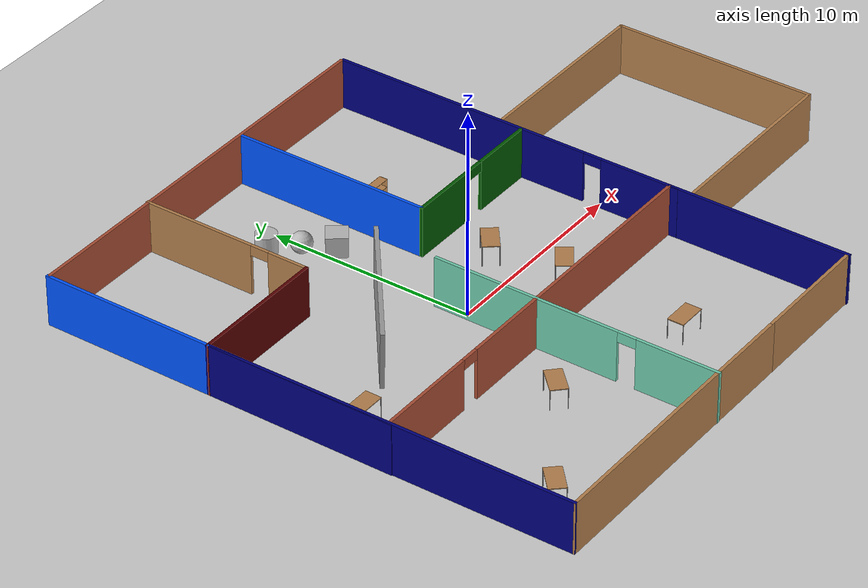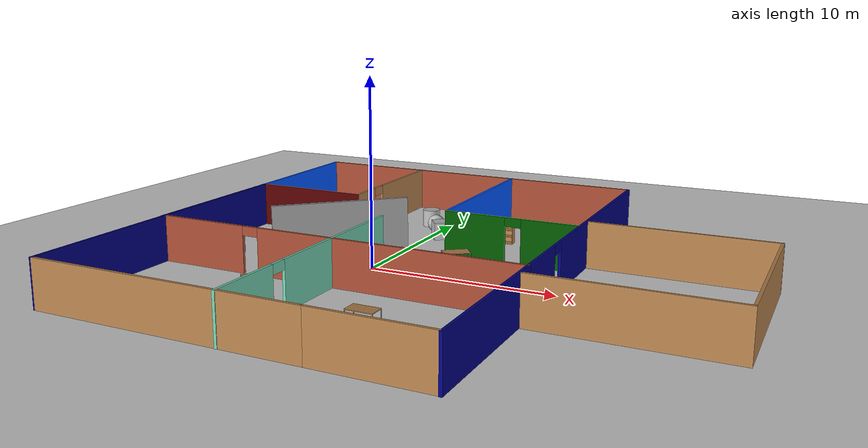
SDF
<sdf version="1.6">
 <world name="default">
  <model name="ground_plane">
   <static>1</static>
   <link name="link">
    <collision name="collision">
     <geometry><plane><normal>0 0 1</normal><size>100 100</size></plane></geometry>
     <surface><friction><ode><mu>100</mu><mu2>50</mu2></ode></friction></surface>
    </collision>
    <visual name="visual">
     <cast_shadows>0</cast_shadows>
     <geometry><plane><normal>0 0 1</normal><size>100 100</size></plane></geometry>
     <material>
      <script><uri>file://media/materials/scripts/gazebo.material</uri><name>Gazebo/Grey</name></script>
     </material>
    </visual>
   </link>
  </model>
  <gravity>0 0 -9.8</gravity>
  <magnetic_field>6e-06 2.3e-05 -4.2e-05</magnetic_field>
  <atmosphere type="adiabatic"/>
  <physics name="default_physics" default="0" type="ode">
   <max_step_size>0.001</max_step_size>
   <real_time_factor>1</real_time_factor>
   <real_time_update_rate>1000</real_time_update_rate>
  </physics>
  <scene><ambient>0.4 0.4 0.4 1</ambient><background>0.7 0.7 0.7 1</background><shadows>1</shadows></scene>
  <spherical_coordinates>
   <surface_model>EARTH_WGS84</surface_model>
   <latitude_deg>0</latitude_deg>
   <longitude_deg>0</longitude_deg>
   <elevation>0</elevation>
   <heading_deg>0</heading_deg>
  </spherical_coordinates>
  <model name="bookshelf">
   <static>1</static>
   <link name="link">
    <inertial><mass>1</mass></inertial>
    <collision name="back">
     <pose>0 0.005 0.6 0 -0 0</pose>
     <geometry><box><size>0.9 0.01 1.2</size></box></geometry>
    </collision>
    <visual name="visual1">
     <pose>0 0.005 0.6 0 -0 0</pose>
     <geometry><box><size>0.9 0.01 1.2</size></box></geometry>
     <material>
      <script><uri>file://media/materials/scripts/gazebo.material</uri><name>Gazebo/Wood</name></script>
     </material>
    </visual>
    <collision name="left_side">
     <pose>0.45 -0.195 0.6 0 -0 0</pose>
     <geometry><box><size>0.02 0.4 1.2</size></box></geometry>
    </collision>
    <visual name="visual2">
     <pose>0.45 -0.195 0.6 0 -0 0</pose>
     <geometry><box><size>0.02 0.4 1.2</size></box></geometry>
     <material>
      <script><uri>file://media/materials/scripts/gazebo.material</uri><name>Gazebo/Wood</name></script>
     </material>
    </visual>
    <collision name="right_side">
     <pose>-0.45 -0.195 0.6 0 -0 0</pose>
     <geometry><box><size>0.02 0.4 1.2</size></box></geometry>
    </collision>
    <visual name="visual3">
     <pose>-0.45 -0.195 0.6 0 -0 0</pose>
     <geometry><box><size>0.02 0.4 1.2</size></box></geometry>
     <material>
      <script><uri>file://media/materials/scripts/gazebo.material</uri><name>Gazebo/Wood</name></script>
     </material>
    </visual>
    <collision name="bottom">
     <pose>0 -0.195 0.03 0 -0 0</pose>
     <geometry><box><size>0.88 0.4 0.06</size></box></geometry>
    </collision>
    <visual name="visual4">
     <pose>0 -0.195 0.03 0 -0 0</pose>
     <geometry><box><size>0.88 0.4 0.06</size></box></geometry>
     <material>
      <script><uri>file://media/materials/scripts/gazebo.material</uri><name>Gazebo/Wood</name></script>
     </material>
    </visual>
    <collision name="top">
     <pose>0 -0.195 1.19 0 -0 0</pose>
     <geometry><box><size>0.88 0.4 0.02</size></box></geometry>
    </collision>
    <visual name="visual5">
     <pose>0 -0.195 1.19 0 -0 0</pose>
     <geometry><box><size>0.88 0.4 0.02</size></box></geometry>
     <material>
      <script><uri>file://media/materials/scripts/gazebo.material</uri><name>Gazebo/Wood</name></script>
     </material>
    </visual>
    <collision name="low_shelf">
     <pose>0 -0.195 0.43 0 -0 0</pose>
     <geometry><box><size>0.88 0.4 0.02</size></box></geometry>
    </collision>
    <visual name="visual6">
     <pose>0 -0.195 0.43 0 -0 0</pose>
     <geometry><box><size>0.88 0.4 0.02</size></box></geometry>
     <material>
      <script><uri>file://media/materials/scripts/gazebo.material</uri><name>Gazebo/Wood</name></script>
     </material>
    </visual>
    <collision name="high_shelf">
     <pose>0 -0.195 0.8 0 -0 0</pose>
     <geometry><box><size>0.88 0.4 0.02</size></box></geometry>
    </collision>
    <visual name="visual7">
     <pose>0 -0.195 0.8 0 -0 0</pose>
     <geometry><box><size>0.88 0.4 0.02</size></box></geometry>
     <material>
      <script><uri>file://media/materials/scripts/gazebo.material</uri><name>Gazebo/Wood</name></script>
     </material>
    </visual>
   </link>
   <pose>4.37362 8.00409 0 0 -0 0</pose>
  </model>
  <model name="table">
   <static>0</static>
   <link name="link">
    <collision name="surface">
     <pose>0 0 1 0 -0 0</pose>
     <geometry><box><size>1.5 0.8 0.03</size></box></geometry>
     <surface><friction><ode><mu>0.6</mu><mu2>0.6</mu2></ode></friction></surface>
    </collision>
    <visual name="visual1">
     <pose>0 0 1 0 -0 0</pose>
     <geometry><box><size>1.4 0.8 0.04</size></box></geometry>
     <material>
      <script><uri>file://media/materials/scripts/gazebo.material</uri><name>Gazebo/Wood</name></script>
     </material>
    </visual>
    <collision name="front_left_leg">
     <pose>0.68 0.38 0.5 0 -0 0</pose>
     <geometry><cylinder><radius>0.02</radius><length>1</length></cylinder></geometry>
    </collision>
    <visual name="front_left_leg">
     <pose>0.68 0.38 0.5 0 -0 0</pose>
     <geometry><cylinder><radius>0.02</radius><length>1</length></cylinder></geometry>
     <material>
      <script><uri>file://media/materials/scripts/gazebo.material</uri><name>Gazebo/Grey</name></script>
     </material>
    </visual>
    <collision name="front_right_leg">
     <pose>0.68 -0.38 0.5 0 -0 0</pose>
     <geometry><cylinder><radius>0.02</radius><length>1</length></cylinder></geometry>
    </collision>
    <visual name="front_right_leg">
     <pose>0.68 -0.38 0.5 0 -0 0</pose>
     <geometry><cylinder><radius>0.02</radius><length>1</length></cylinder></geometry>
     <material>
      <script><uri>file://media/materials/scripts/gazebo.material</uri><name>Gazebo/Grey</name></script>
     </material>
    </visual>
    <collision name="back_right_leg">
     <pose>-0.68 -0.38 0.5 0 -0 0</pose>
     <geometry><cylinder><radius>0.02</radius><length>1</length></cylinder></geometry>
    </collision>
    <visual name="back_right_leg">
     <pose>-0.68 -0.38 0.5 0 -0 0</pose>
     <geometry><cylinder><radius>0.02</radius><length>1</length></cylinder></geometry>
     <material>
      <script><uri>file://media/materials/scripts/gazebo.material</uri><name>Gazebo/Grey</name></script>
     </material>
    </visual>
    <collision name="back_left_leg">
     <pose>-0.68 0.38 0.5 0 -0 0</pose>
     <geometry><cylinder><radius>0.02</radius><length>1</length></cylinder></geometry>
    </collision>
    <visual name="back_left_leg">
     <pose>-0.68 0.38 0.5 0 -0 0</pose>
     <geometry><cylinder><radius>0.02</radius><length>1</length></cylinder></geometry>
     <material>
      <script><uri>file://media/materials/scripts/gazebo.material</uri><name>Gazebo/Grey</name></script>
     </material>
    </visual>
    <inertial>
     <inertia><ixx>1</ixx><ixy>0</ixy><ixz>0</ixz><iyy>1</iyy><iyz>0</iyz><izz>1</izz></inertia>
     <mass>1</mass>
    </inertial>
   </link>
   <pose>-8.45641 -0.835319 -9e-06 0 -0 0</pose>
  </model>
  <model name="textured_shapes">
   <pose>-0.307519 8.3938 0.5 0 -0 0.64384</pose>
   <link name="box">
    <pose>0 -1.5 0 0 -0 0</pose>
    <collision name="collision"><geometry><box><size>1 1 1</size></box></geometry></collision>
    <visual name="visual">
     <geometry><box><size>1 1 1</size></box></geometry>
     <material>
      <script>
       <uri>model://textured_shapes/materials/scripts</uri>
       <uri>model://textured_shapes/materials/textures</uri>
       <name>TexturedShape/Squares</name>
      </script>
     </material>
    </visual>
    <inertial>
     <inertia><ixx>1</ixx><ixy>0</ixy><ixz>0</ixz><iyy>1</iyy><iyz>0</iyz><izz>1</izz></inertia>
     <mass>1</mass>
    </inertial>
   </link>
   <link name="sphere">
    <collision name="collision"><geometry><sphere><radius>0.5</radius></sphere></geometry></collision>
    <visual name="visual">
     <geometry><sphere><radius>0.5</radius></sphere></geometry>
     <material>
      <script>
       <uri>model://textured_shapes/materials/scripts</uri>
       <uri>model://textured_shapes/materials/textures</uri>
       <name>TexturedShape/Squares</name>
      </script>
     </material>
    </visual>
    <inertial>
     <inertia><ixx>1</ixx><ixy>0</ixy><ixz>0</ixz><iyy>1</iyy><iyz>0</iyz><izz>1</izz></inertia>
     <mass>1</mass>
    </inertial>
   </link>
   <link name="cylinder">
    <pose>0 1.5 0 0 -0 0</pose>
    <collision name="collision">
     <geometry><cylinder><radius>0.5</radius><length>1</length></cylinder></geometry>
    </collision>
    <visual name="visual">
     <geometry><cylinder><radius>0.5</radius><length>1</length></cylinder></geometry>
     <material>
      <script>
       <uri>model://textured_shapes/materials/scripts</uri>
       <uri>model://textured_shapes/materials/textures</uri>
       <name>TexturedShape/Squares</name>
      </script>
     </material>
    </visual>
    <inertial>
     <inertia><ixx>1</ixx><ixy>0</ixy><ixz>0</ixz><iyy>1</iyy><iyz>0</iyz><izz>1</izz></inertia>
     <mass>1</mass>
    </inertial>
   </link>
  </model>
  <model name="table_0">
   <static>0</static>
   <link name="link">
    <collision name="surface">
     <pose>0 0 1 0 -0 0</pose>
     <geometry><box><size>1.5 0.8 0.03</size></box></geometry>
     <surface><friction><ode><mu>0.6</mu><mu2>0.6</mu2></ode></friction></surface>
    </collision>
    <visual name="visual1">
     <pose>0 0 1 0 -0 0</pose>
     <geometry><box><size>1.4 0.8 0.04</size></box></geometry>
     <material>
      <script><uri>file://media/materials/scripts/gazebo.material</uri><name>Gazebo/Wood</name></script>
     </material>
    </visual>
    <collision name="front_left_leg">
     <pose>0.68 0.38 0.5 0 -0 0</pose>
     <geometry><cylinder><radius>0.02</radius><length>1</length></cylinder></geometry>
    </collision>
    <visual name="front_left_leg">
     <pose>0.68 0.38 0.5 0 -0 0</pose>
     <geometry><cylinder><radius>0.02</radius><length>1</length></cylinder></geometry>
     <material>
      <script><uri>file://media/materials/scripts/gazebo.material</uri><name>Gazebo/Grey</name></script>
     </material>
    </visual>
    <collision name="front_right_leg">
     <pose>0.68 -0.38 0.5 0 -0 0</pose>
     <geometry><cylinder><radius>0.02</radius><length>1</length></cylinder></geometry>
    </collision>
    <visual name="front_right_leg">
     <pose>0.68 -0.38 0.5 0 -0 0</pose>
     <geometry><cylinder><radius>0.02</radius><length>1</length></cylinder></geometry>
     <material>
      <script><uri>file://media/materials/scripts/gazebo.material</uri><name>Gazebo/Grey</name></script>
     </material>
    </visual>
    <collision name="back_right_leg">
     <pose>-0.68 -0.38 0.5 0 -0 0</pose>
     <geometry><cylinder><radius>0.02</radius><length>1</length></cylinder></geometry>
    </collision>
    <visual name="back_right_leg">
     <pose>-0.68 -0.38 0.5 0 -0 0</pose>
     <geometry><cylinder><radius>0.02</radius><length>1</length></cylinder></geometry>
     <material>
      <script><uri>file://media/materials/scripts/gazebo.material</uri><name>Gazebo/Grey</name></script>
     </material>
    </visual>
    <collision name="back_left_leg">
     <pose>-0.68 0.38 0.5 0 -0 0</pose>
     <geometry><cylinder><radius>0.02</radius><length>1</length></cylinder></geometry>
    </collision>
    <visual name="back_left_leg">
     <pose>-0.68 0.38 0.5 0 -0 0</pose>
     <geometry><cylinder><radius>0.02</radius><length>1</length></cylinder></geometry>
     <material>
      <script><uri>file://media/materials/scripts/gazebo.material</uri><name>Gazebo/Grey</name></script>
     </material>
    </visual>
    <inertial>
     <inertia><ixx>1</ixx><ixy>0</ixy><ixz>0</ixz><iyy>1</iyy><iyz>0</iyz><izz>1</izz></inertia>
     <mass>1</mass>
    </inertial>
   </link>
   <pose>4.11112 -8.08132 -9e-06 0 -0 0</pose>
  </model>
  <model name="grey_wall">
   <static>1</static>
   <link name="link">
    <pose>0 0 1.4 0 -0 0</pose>
    <collision name="collision"><geometry><box><size>7.5 0.2 2.8</size></box></geometry></collision>
    <visual name="visual">
     <cast_shadows>0</cast_shadows>
     <geometry><box><size>7.5 0.2 2.8</size></box></geometry>
     <material>
      <script>
       <uri>model://grey_wall/materials/scripts</uri>
       <uri>model://grey_wall/materials/textures</uri>
       <name>vrc/grey_wall</name>
      </script>
     </material>
    </visual>
   </link>
   <pose>-3.18514 2.23987 4e-06 0.01417 -0.022146 0.663578</pose>
  </model>
  <model name="table_1">
   <static>0</static>
   <link name="link">
    <collision name="surface">
     <pose>0 0 1 0 -0 0</pose>
     <geometry><box><size>1.5 0.8 0.03</size></box></geometry>
     <surface><friction><ode><mu>0.6</mu><mu2>0.6</mu2></ode></friction></surface>
    </collision>
    <visual name="visual1">
     <pose>0 0 1 0 -0 0</pose>
     <geometry><box><size>1.4 0.8 0.04</size></box></geometry>
     <material>
      <script><uri>file://media/materials/scripts/gazebo.material</uri><name>Gazebo/Wood</name></script>
     </material>
    </visual>
    <collision name="front_left_leg">
     <pose>0.68 0.38 0.5 0 -0 0</pose>
     <geometry><cylinder><radius>0.02</radius><length>1</length></cylinder></geometry>
    </collision>
    <visual name="front_left_leg">
     <pose>0.68 0.38 0.5 0 -0 0</pose>
     <geometry><cylinder><radius>0.02</radius><length>1</length></cylinder></geometry>
     <material>
      <script><uri>file://media/materials/scripts/gazebo.material</uri><name>Gazebo/Grey</name></script>
     </material>
    </visual>
    <collision name="front_right_leg">
     <pose>0.68 -0.38 0.5 0 -0 0</pose>
     <geometry><cylinder><radius>0.02</radius><length>1</length></cylinder></geometry>
    </collision>
    <visual name="front_right_leg">
     <pose>0.68 -0.38 0.5 0 -0 0</pose>
     <geometry><cylinder><radius>0.02</radius><length>1</length></cylinder></geometry>
     <material>
      <script><uri>file://media/materials/scripts/gazebo.material</uri><name>Gazebo/Grey</name></script>
     </material>
    </visual>
    <collision name="back_right_leg">
     <pose>-0.68 -0.38 0.5 0 -0 0</pose>
     <geometry><cylinder><radius>0.02</radius><length>1</length></cylinder></geometry>
    </collision>
    <visual name="back_right_leg">
     <pose>-0.68 -0.38 0.5 0 -0 0</pose>
     <geometry><cylinder><radius>0.02</radius><length>1</length></cylinder></geometry>
     <material>
      <script><uri>file://media/materials/scripts/gazebo.material</uri><name>Gazebo/Grey</name></script>
     </material>
    </visual>
    <collision name="back_left_leg">
     <pose>-0.68 0.38 0.5 0 -0 0</pose>
     <geometry><cylinder><radius>0.02</radius><length>1</length></cylinder></geometry>
    </collision>
    <visual name="back_left_leg">
     <pose>-0.68 0.38 0.5 0 -0 0</pose>
     <geometry><cylinder><radius>0.02</radius><length>1</length></cylinder></geometry>
     <material>
      <script><uri>file://media/materials/scripts/gazebo.material</uri><name>Gazebo/Grey</name></script>
     </material>
    </visual>
    <inertial>
     <inertia><ixx>1</ixx><ixy>0</ixy><ixz>0</ixz><iyy>1</iyy><iyz>0</iyz><izz>1</izz></inertia>
     <mass>1</mass>
    </inertial>
   </link>
   <pose>4.6721 -1.71836 -1e-05 0 -0 0.603298</pose>
  </model>
  <model name="table_2">
   <static>0</static>
   <link name="link">
    <collision name="surface">
     <pose>0 0 1 0 -0 0</pose>
     <geometry><box><size>1.5 0.8 0.03</size></box></geometry>
     <surface><friction><ode><mu>0.6</mu><mu2>0.6</mu2></ode></friction></surface>
    </collision>
    <visual name="visual1">
     <pose>0 0 1 0 -0 0</pose>
     <geometry><box><size>1.4 0.8 0.04</size></box></geometry>
     <material>
      <script><uri>file://media/materials/scripts/gazebo.material</uri><name>Gazebo/Wood</name></script>
     </material>
    </visual>
    <collision name="front_left_leg">
     <pose>0.68 0.38 0.5 0 -0 0</pose>
     <geometry><cylinder><radius>0.02</radius><length>1</length></cylinder></geometry>
    </collision>
    <visual name="front_left_leg">
     <pose>0.68 0.38 0.5 0 -0 0</pose>
     <geometry><cylinder><radius>0.02</radius><length>1</length></cylinder></geometry>
     <material>
      <script><uri>file://media/materials/scripts/gazebo.material</uri><name>Gazebo/Grey</name></script>
     </material>
    </visual>
    <collision name="front_right_leg">
     <pose>0.68 -0.38 0.5 0 -0 0</pose>
     <geometry><cylinder><radius>0.02</radius><length>1</length></cylinder></geometry>
    </collision>
    <visual name="front_right_leg">
     <pose>0.68 -0.38 0.5 0 -0 0</pose>
     <geometry><cylinder><radius>0.02</radius><length>1</length></cylinder></geometry>
     <material>
      <script><uri>file://media/materials/scripts/gazebo.material</uri><name>Gazebo/Grey</name></script>
     </material>
    </visual>
    <collision name="back_right_leg">
     <pose>-0.68 -0.38 0.5 0 -0 0</pose>
     <geometry><cylinder><radius>0.02</radius><length>1</length></cylinder></geometry>
    </collision>
    <visual name="back_right_leg">
     <pose>-0.68 -0.38 0.5 0 -0 0</pose>
     <geometry><cylinder><radius>0.02</radius><length>1</length></cylinder></geometry>
     <material>
      <script><uri>file://media/materials/scripts/gazebo.material</uri><name>Gazebo/Grey</name></script>
     </material>
    </visual>
    <collision name="back_left_leg">
     <pose>-0.68 0.38 0.5 0 -0 0</pose>
     <geometry><cylinder><radius>0.02</radius><length>1</length></cylinder></geometry>
    </collision>
    <visual name="back_left_leg">
     <pose>-0.68 0.38 0.5 0 -0 0</pose>
     <geometry><cylinder><radius>0.02</radius><length>1</length></cylinder></geometry>
     <material>
      <script><uri>file://media/materials/scripts/gazebo.material</uri><name>Gazebo/Grey</name></script>
     </material>
    </visual>
    <inertial>
     <inertia><ixx>1</ixx><ixy>0</ixy><ixz>0</ixz><iyy>1</iyy><iyz>0</iyz><izz>1</izz></inertia>
     <mass>1</mass>
    </inertial>
   </link>
   <pose>4.02933 1.6454 -1e-05 0 -0 0.661845</pose>
  </model>
  <model name="table_0_clone">
   <static>0</static>
   <link name="link">
    <collision name="surface">
     <pose>0 0 1 0 -0 0</pose>
     <geometry><box><size>1.5 0.8 0.03</size></box></geometry>
     <surface><friction><ode><mu>0.6</mu><mu2>0.6</mu2></ode></friction></surface>
    </collision>
    <visual name="visual1">
     <pose>0 0 1 0 -0 0</pose>
     <geometry><box><size>1.4 0.8 0.04</size></box></geometry>
     <material>
      <script><uri>file://media/materials/scripts/gazebo.material</uri><name>Gazebo/Wood</name></script>
     </material>
    </visual>
    <collision name="front_left_leg">
     <pose>0.68 0.38 0.5 0 -0 0</pose>
     <geometry><cylinder><radius>0.02</radius><length>1</length></cylinder></geometry>
    </collision>
    <visual name="front_left_leg">
     <pose>0.68 0.38 0.5 0 -0 0</pose>
     <geometry><cylinder><radius>0.02</radius><length>1</length></cylinder></geometry>
     <material>
      <script><uri>file://media/materials/scripts/gazebo.material</uri><name>Gazebo/Grey</name></script>
     </material>
    </visual>
    <collision name="front_right_leg">
     <pose>0.68 -0.38 0.5 0 -0 0</pose>
     <geometry><cylinder><radius>0.02</radius><length>1</length></cylinder></geometry>
    </collision>
    <visual name="front_right_leg">
     <pose>0.68 -0.38 0.5 0 -0 0</pose>
     <geometry><cylinder><radius>0.02</radius><length>1</length></cylinder></geometry>
     <material>
      <script><uri>file://media/materials/scripts/gazebo.material</uri><name>Gazebo/Grey</name></script>
     </material>
    </visual>
    <collision name="back_right_leg">
     <pose>-0.68 -0.38 0.5 0 -0 0</pose>
     <geometry><cylinder><radius>0.02</radius><length>1</length></cylinder></geometry>
    </collision>
    <visual name="back_right_leg">
     <pose>-0.68 -0.38 0.5 0 -0 0</pose>
     <geometry><cylinder><radius>0.02</radius><length>1</length></cylinder></geometry>
     <material>
      <script><uri>file://media/materials/scripts/gazebo.material</uri><name>Gazebo/Grey</name></script>
     </material>
    </visual>
    <collision name="back_left_leg">
     <pose>-0.68 0.38 0.5 0 -0 0</pose>
     <geometry><cylinder><radius>0.02</radius><length>1</length></cylinder></geometry>
    </collision>
    <visual name="back_left_leg">
     <pose>-0.68 0.38 0.5 0 -0 0</pose>
     <geometry><cylinder><radius>0.02</radius><length>1</length></cylinder></geometry>
     <material>
      <script><uri>file://media/materials/scripts/gazebo.material</uri><name>Gazebo/Grey</name></script>
     </material>
    </visual>
    <inertial>
     <inertia><ixx>1</ixx><ixy>0</ixy><ixz>0</ixz><iyy>1</iyy><iyz>0</iyz><izz>1</izz></inertia>
     <mass>1</mass>
    </inertial>
   </link>
   <pose>-8.04629 -9.85646 -1e-06 -2e-06 -0 0.74218</pose>
  </model>
  <model name="table_0_clone_0">
   <static>0</static>
   <link name="link">
    <collision name="surface">
     <pose>0 0 1 0 -0 0</pose>
     <geometry><box><size>1.5 0.8 0.03</size></box></geometry>
     <surface><friction><ode><mu>0.6</mu><mu2>0.6</mu2></ode></friction></surface>
    </collision>
    <visual name="visual1">
     <pose>0 0 1 0 -0 0</pose>
     <geometry><box><size>1.4 0.8 0.04</size></box></geometry>
     <material>
      <script><uri>file://media/materials/scripts/gazebo.material</uri><name>Gazebo/Wood</name></script>
     </material>
    </visual>
    <collision name="front_left_leg">
     <pose>0.68 0.38 0.5 0 -0 0</pose>
     <geometry><cylinder><radius>0.02</radius><length>1</length></cylinder></geometry>
    </collision>
    <visual name="front_left_leg">
     <pose>0.68 0.38 0.5 0 -0 0</pose>
     <geometry><cylinder><radius>0.02</radius><length>1</length></cylinder></geometry>
     <material>
      <script><uri>file://media/materials/scripts/gazebo.material</uri><name>Gazebo/Grey</name></script>
     </material>
    </visual>
    <collision name="front_right_leg">
     <pose>0.68 -0.38 0.5 0 -0 0</pose>
     <geometry><cylinder><radius>0.02</radius><length>1</length></cylinder></geometry>
    </collision>
    <visual name="front_right_leg">
     <pose>0.68 -0.38 0.5 0 -0 0</pose>
     <geometry><cylinder><radius>0.02</radius><length>1</length></cylinder></geometry>
     <material>
      <script><uri>file://media/materials/scripts/gazebo.material</uri><name>Gazebo/Grey</name></script>
     </material>
    </visual>
    <collision name="back_right_leg">
     <pose>-0.68 -0.38 0.5 0 -0 0</pose>
     <geometry><cylinder><radius>0.02</radius><length>1</length></cylinder></geometry>
    </collision>
    <visual name="back_right_leg">
     <pose>-0.68 -0.38 0.5 0 -0 0</pose>
     <geometry><cylinder><radius>0.02</radius><length>1</length></cylinder></geometry>
     <material>
      <script><uri>file://media/materials/scripts/gazebo.material</uri><name>Gazebo/Grey</name></script>
     </material>
    </visual>
    <collision name="back_left_leg">
     <pose>-0.68 0.38 0.5 0 -0 0</pose>
     <geometry><cylinder><radius>0.02</radius><length>1</length></cylinder></geometry>
    </collision>
    <visual name="back_left_leg">
     <pose>-0.68 0.38 0.5 0 -0 0</pose>
     <geometry><cylinder><radius>0.02</radius><length>1</length></cylinder></geometry>
     <material>
      <script><uri>file://media/materials/scripts/gazebo.material</uri><name>Gazebo/Grey</name></script>
     </material>
    </visual>
    <inertial>
     <inertia><ixx>1</ixx><ixy>0</ixy><ixz>0</ixz><iyy>1</iyy><iyz>0</iyz><izz>1</izz></inertia>
     <mass>1</mass>
    </inertial>
   </link>
   <pose>-2.70032 -6.28133 -8e-06 -1e-06 -0 0.788199</pose>
  </model>
  <model name="RGB_Walls_And_Doors">
   <link name="Wall_13">
    <pose>-4.768 13.0532 0 0 -0 3.14159</pose>
    <visual name="Wall_13_Visual">
     <pose>0 0 1.25 0 -0 0</pose>
     <geometry><box><size>20.35 0.15 2.5</size></box></geometry>
     <material>
      <script><uri>file://media/materials/scripts/gazebo.material</uri><name>Gazebo/Bricks</name></script>
      <ambient>1 1 1 1</ambient>
      <diffuse>1 1 1 1</diffuse>
      <specular>0.2 0.2 0.2 1</specular>
      <emissive>0 0 0 1</emissive>
     </material>
    </visual>
    <collision name="Wall_13_Collision">
     <pose>0 0 1.25 0 -0 0</pose>
     <geometry><box><size>20.35 0.15 2.5</size></box></geometry>
     <surface>
      <friction>
       <ode><mu>1</mu><mu2>1</mu2><fdir1>0 0 0</fdir1><slip1>0</slip1><slip2>0</slip2></ode>
       <torsional>
        <coefficient>1</coefficient>
        <patch_radius>0</patch_radius>
        <surface_radius>0</surface_radius>
        <use_patch_radius>1</use_patch_radius>
        <ode><slip>0</slip></ode>
       </torsional>
      </friction>
      <bounce><restitution_coefficient>0</restitution_coefficient><threshold>1e+06</threshold></bounce>
      <contact>
       <collide_without_contact>0</collide_without_contact>
       <collide_without_contact_bitmask>1</collide_without_contact_bitmask>
       <collide_bitmask>1</collide_bitmask>
       <ode>
        <soft_cfm>0</soft_cfm>
        <soft_erp>0.2</soft_erp>
        <kp>1e+13</kp>
        <kd>1</kd>
        <max_vel>0.01</max_vel>
        <min_depth>0</min_depth>
       </ode>
       <bullet>
        <split_impulse>1</split_impulse>
        <split_impulse_penetration_threshold>-0.01</split_impulse_penetration_threshold>
        <soft_cfm>0</soft_cfm>
        <soft_erp>0.2</soft_erp>
        <kp>1e+13</kp>
        <kd>1</kd>
       </bullet>
      </contact>
     </surface>
    </collision>
   </link>
   <link name="Wall_15">
    <pose>-7.693 -13.0468 0 0 -0 3.14159</pose>
    <visual name="Wall_15_Visual">
     <pose>0 0 1.25 0 -0 0</pose>
     <geometry><box><size>14.5 0.15 2.5</size></box></geometry>
     <material>
      <script><uri>file://media/materials/scripts/gazebo.material</uri><name>Gazebo/Wood</name></script>
      <ambient>1 1 1 1</ambient>
      <diffuse>1 1 1 1</diffuse>
      <specular>0.2 0.2 0.2 1</specular>
      <emissive>0 0 0 1</emissive>
     </material>
    </visual>
    <collision name="Wall_15_Collision">
     <pose>0 0 1.25 0 -0 0</pose>
     <geometry><box><size>14.5 0.15 2.5</size></box></geometry>
     <surface>
      <friction>
       <ode><mu>1</mu><mu2>1</mu2><fdir1>0 0 0</fdir1><slip1>0</slip1><slip2>0</slip2></ode>
       <torsional>
        <coefficient>1</coefficient>
        <patch_radius>0</patch_radius>
        <surface_radius>0</surface_radius>
        <use_patch_radius>1</use_patch_radius>
        <ode><slip>0</slip></ode>
       </torsional>
      </friction>
      <bounce><restitution_coefficient>0</restitution_coefficient><threshold>1e+06</threshold></bounce>
      <contact>
       <collide_without_contact>0</collide_without_contact>
       <collide_without_contact_bitmask>1</collide_without_contact_bitmask>
       <collide_bitmask>1</collide_bitmask>
       <ode>
        <soft_cfm>0</soft_cfm>
        <soft_erp>0.2</soft_erp>
        <kp>1e+13</kp>
        <kd>1</kd>
        <max_vel>0.01</max_vel>
        <min_depth>0</min_depth>
       </ode>
       <bullet>
        <split_impulse>1</split_impulse>
        <split_impulse_penetration_threshold>-0.01</split_impulse_penetration_threshold>
        <soft_cfm>0</soft_cfm>
        <soft_erp>0.2</soft_erp>
        <kp>1e+13</kp>
        <kd>1</kd>
       </bullet>
      </contact>
     </surface>
    </collision>
   </link>
   <link name="Wall_19">
    <pose>14.9404 -0.436235 0 0 -0 1.5708</pose>
    <visual name="Wall_19_Visual">
     <pose>0 0 1.25 0 -0 0</pose>
     <geometry><box><size>10 0.15 2.5</size></box></geometry>
     <material>
      <script><uri>file://media/materials/scripts/gazebo.material</uri><name>Gazebo/Wood</name></script>
      <ambient>1 1 1 1</ambient>
      <diffuse>1 1 1 1</diffuse>
      <specular>0.2 0.2 0.2 1</specular>
      <emissive>0 0 0 1</emissive>
     </material>
    </visual>
    <collision name="Wall_19_Collision">
     <pose>0 0 1.25 0 -0 0</pose>
     <geometry><box><size>10 0.15 2.5</size></box></geometry>
     <surface>
      <friction>
       <ode><mu>1</mu><mu2>1</mu2><fdir1>0 0 0</fdir1><slip1>0</slip1><slip2>0</slip2></ode>
       <torsional>
        <coefficient>1</coefficient>
        <patch_radius>0</patch_radius>
        <surface_radius>0</surface_radius>
        <use_patch_radius>1</use_patch_radius>
        <ode><slip>0</slip></ode>
       </torsional>
      </friction>
      <bounce><restitution_coefficient>0</restitution_coefficient><threshold>1e+06</threshold></bounce>
      <contact>
       <collide_without_contact>0</collide_without_contact>
       <collide_without_contact_bitmask>1</collide_without_contact_bitmask>
       <collide_bitmask>1</collide_bitmask>
       <ode>
        <soft_cfm>0</soft_cfm>
        <soft_erp>0.2</soft_erp>
        <kp>1e+13</kp>
        <kd>1</kd>
        <max_vel>0.01</max_vel>
        <min_depth>0</min_depth>
       </ode>
       <bullet>
        <split_impulse>1</split_impulse>
        <split_impulse_penetration_threshold>-0.01</split_impulse_penetration_threshold>
        <soft_cfm>0</soft_cfm>
        <soft_erp>0.2</soft_erp>
        <kp>1e+13</kp>
        <kd>1</kd>
       </bullet>
      </contact>
     </surface>
    </collision>
   </link>
   <link name="Wall_23">
    <pose>1.6654 3.38876 0 0 -0 3.14159</pose>
    <visual name="Wall_23_Visual_0">
     <pose>-2.17368 0 1.25 0 -0 0</pose>
     <geometry><box><size>3.15264 0.15 2.5</size></box></geometry>
     <material>
      <script><uri>file://media/materials/scripts/gazebo.material</uri><name>Gazebo/Grey</name></script>
      <ambient>0 0.333333 0 1</ambient>
      <diffuse>0.7 0.7 0.7 1</diffuse>
      <specular>0.01 0.01 0.01 1</specular>
      <emissive>0 0 0 1</emissive>
     </material>
    </visual>
    <visual name="Wall_23_Visual_1">
     <pose>2.02632 0 1.25 0 -0 0</pose>
     <geometry><box><size>3.44736 0.15 2.5</size></box></geometry>
     <material>
      <script><uri>file://media/materials/scripts/gazebo.material</uri><name>Gazebo/Grey</name></script>
      <ambient>0 0.333333 0 1</ambient>
      <diffuse>0.7 0.7 0.7 1</diffuse>
      <specular>0.01 0.01 0.01 1</specular>
      <emissive>0 0 0 1</emissive>
     </material>
    </visual>
    <visual name="Wall_23_Visual_2">
     <pose>-0.147364 0 2.25 0 -0 0</pose>
     <geometry><box><size>0.9 0.15 0.5</size></box></geometry>
     <material>
      <script><uri>file://media/materials/scripts/gazebo.material</uri><name>Gazebo/Grey</name></script>
      <ambient>0 0.333333 0 1</ambient>
      <diffuse>0.7 0.7 0.7 1</diffuse>
      <specular>0.01 0.01 0.01 1</specular>
      <emissive>0 0 0 1</emissive>
     </material>
    </visual>
    <collision name="Wall_23_Collision_0">
     <pose>-2.17368 0 1.25 0 -0 0</pose>
     <geometry><box><size>3.15264 0.15 2.5</size></box></geometry>
     <surface>
      <friction>
       <ode><mu>1</mu><mu2>1</mu2><fdir1>0 0 0</fdir1><slip1>0</slip1><slip2>0</slip2></ode>
       <torsional>
        <coefficient>1</coefficient>
        <patch_radius>0</patch_radius>
        <surface_radius>0</surface_radius>
        <use_patch_radius>1</use_patch_radius>
        <ode><slip>0</slip></ode>
       </torsional>
      </friction>
      <bounce><restitution_coefficient>0</restitution_coefficient><threshold>1e+06</threshold></bounce>
      <contact>
       <collide_without_contact>0</collide_without_contact>
       <collide_without_contact_bitmask>1</collide_without_contact_bitmask>
       <collide_bitmask>1</collide_bitmask>
       <ode>
        <soft_cfm>0</soft_cfm>
        <soft_erp>0.2</soft_erp>
        <kp>1e+13</kp>
        <kd>1</kd>
        <max_vel>0.01</max_vel>
        <min_depth>0</min_depth>
       </ode>
       <bullet>
        <split_impulse>1</split_impulse>
        <split_impulse_penetration_threshold>-0.01</split_impulse_penetration_threshold>
        <soft_cfm>0</soft_cfm>
        <soft_erp>0.2</soft_erp>
        <kp>1e+13</kp>
        <kd>1</kd>
       </bullet>
      </contact>
     </surface>
    </collision>
    <collision name="Wall_23_Collision_1">
     <pose>2.02632 0 1.25 0 -0 0</pose>
     <geometry><box><size>3.44736 0.15 2.5</size></box></geometry>
     <surface>
      <friction>
       <ode><mu>1</mu><mu2>1</mu2><fdir1>0 0 0</fdir1><slip1>0</slip1><slip2>0</slip2></ode>
       <torsional>
        <coefficient>1</coefficient>
        <patch_radius>0</patch_radius>
        <surface_radius>0</surface_radius>
        <use_patch_radius>1</use_patch_radius>
        <ode><slip>0</slip></ode>
       </torsional>
      </friction>
      <bounce><restitution_coefficient>0</restitution_coefficient><threshold>1e+06</threshold></bounce>
      <contact>
       <collide_without_contact>0</collide_without_contact>
       <collide_without_contact_bitmask>1</collide_without_contact_bitmask>
       <collide_bitmask>1</collide_bitmask>
       <ode>
        <soft_cfm>0</soft_cfm>
        <soft_erp>0.2</soft_erp>
        <kp>1e+13</kp>
        <kd>1</kd>
        <max_vel>0.01</max_vel>
        <min_depth>0</min_depth>
       </ode>
       <bullet>
        <split_impulse>1</split_impulse>
        <split_impulse_penetration_threshold>-0.01</split_impulse_penetration_threshold>
        <soft_cfm>0</soft_cfm>
        <soft_erp>0.2</soft_erp>
        <kp>1e+13</kp>
        <kd>1</kd>
       </bullet>
      </contact>
     </surface>
    </collision>
    <collision name="Wall_23_Collision_2">
     <pose>-0.147364 0 2.25 0 -0 0</pose>
     <geometry><box><size>0.9 0.15 0.5</size></box></geometry>
     <surface>
      <friction>
       <ode><mu>1</mu><mu2>1</mu2><fdir1>0 0 0</fdir1><slip1>0</slip1><slip2>0</slip2></ode>
       <torsional>
        <coefficient>1</coefficient>
        <patch_radius>0</patch_radius>
        <surface_radius>0</surface_radius>
        <use_patch_radius>1</use_patch_radius>
        <ode><slip>0</slip></ode>
       </torsional>
      </friction>
      <bounce><restitution_coefficient>0</restitution_coefficient><threshold>1e+06</threshold></bounce>
      <contact>
       <collide_without_contact>0</collide_without_contact>
       <collide_without_contact_bitmask>1</collide_without_contact_bitmask>
       <collide_bitmask>1</collide_bitmask>
       <ode>
        <soft_cfm>0</soft_cfm>
        <soft_erp>0.2</soft_erp>
        <kp>1e+13</kp>
        <kd>1</kd>
        <max_vel>0.01</max_vel>
        <min_depth>0</min_depth>
       </ode>
       <bullet>
        <split_impulse>1</split_impulse>
        <split_impulse_penetration_threshold>-0.01</split_impulse_penetration_threshold>
        <soft_cfm>0</soft_cfm>
        <soft_erp>0.2</soft_erp>
        <kp>1e+13</kp>
        <kd>1</kd>
       </bullet>
      </contact>
     </surface>
    </collision>
   </link>
   <link name="Wall_24">
    <pose>-2.0096 8.18877 0 0 -0 1.5708</pose>
    <visual name="Wall_24_Visual">
     <pose>0 0 1.25 0 -0 0</pose>
     <geometry><box><size>9.75 0.15 2.5</size></box></geometry>
     <material>
      <script><uri>file://media/materials/scripts/gazebo.material</uri><name>Gazebo/Grey</name></script>
      <ambient>0 0.333333 1 1</ambient>
      <diffuse>0.7 0.7 0.7 1</diffuse>
      <specular>0.01 0.01 0.01 1</specular>
      <emissive>0 0 0 1</emissive>
     </material>
    </visual>
    <collision name="Wall_24_Collision">
     <pose>0 0 1.25 0 -0 0</pose>
     <geometry><box><size>9.75 0.15 2.5</size></box></geometry>
     <surface>
      <friction>
       <ode><mu>1</mu><mu2>1</mu2><fdir1>0 0 0</fdir1><slip1>0</slip1><slip2>0</slip2></ode>
       <torsional>
        <coefficient>1</coefficient>
        <patch_radius>0</patch_radius>
        <surface_radius>0</surface_radius>
        <use_patch_radius>1</use_patch_radius>
        <ode><slip>0</slip></ode>
       </torsional>
      </friction>
      <bounce><restitution_coefficient>0</restitution_coefficient><threshold>1e+06</threshold></bounce>
      <contact>
       <collide_without_contact>0</collide_without_contact>
       <collide_without_contact_bitmask>1</collide_without_contact_bitmask>
       <collide_bitmask>1</collide_bitmask>
       <ode>
        <soft_cfm>0</soft_cfm>
        <soft_erp>0.2</soft_erp>
        <kp>1e+13</kp>
        <kd>1</kd>
        <max_vel>0.01</max_vel>
        <min_depth>0</min_depth>
       </ode>
       <bullet>
        <split_impulse>1</split_impulse>
        <split_impulse_penetration_threshold>-0.01</split_impulse_penetration_threshold>
        <soft_cfm>0</soft_cfm>
        <soft_erp>0.2</soft_erp>
        <kp>1e+13</kp>
        <kd>1</kd>
       </bullet>
      </contact>
     </surface>
    </collision>
   </link>
   <link name="Wall_32">
    <pose>-8.34009 8.91706 0 0 -0 1.5708</pose>
    <visual name="Wall_32_Visual_0">
     <pose>-3.23654 0 1.25 0 -0 0</pose>
     <geometry><box><size>2.02691 0.15 2.5</size></box></geometry>
     <material>
      <script><uri>file://media/materials/scripts/gazebo.material</uri><name>Gazebo/Wood</name></script>
      <ambient>1 1 1 1</ambient>
      <diffuse>1 1 1 1</diffuse>
      <specular>0.2 0.2 0.2 1</specular>
      <emissive>0 0 0 1</emissive>
     </material>
    </visual>
    <visual name="Wall_32_Visual_1">
     <pose>1.46346 0 1.25 0 -0 0</pose>
     <geometry><box><size>5.57309 0.15 2.5</size></box></geometry>
     <material>
      <script><uri>file://media/materials/scripts/gazebo.material</uri><name>Gazebo/Wood</name></script>
      <ambient>1 1 1 1</ambient>
      <diffuse>1 1 1 1</diffuse>
      <specular>0.2 0.2 0.2 1</specular>
      <emissive>0 0 0 1</emissive>
     </material>
    </visual>
    <visual name="Wall_32_Visual_2">
     <pose>-1.77309 0 2.25 0 -0 0</pose>
     <geometry><box><size>0.9 0.15 0.5</size></box></geometry>
     <material>
      <script><uri>file://media/materials/scripts/gazebo.material</uri><name>Gazebo/Wood</name></script>
      <ambient>1 1 1 1</ambient>
      <diffuse>1 1 1 1</diffuse>
      <specular>0.2 0.2 0.2 1</specular>
      <emissive>0 0 0 1</emissive>
     </material>
    </visual>
    <collision name="Wall_32_Collision_0">
     <pose>-3.23654 0 1.25 0 -0 0</pose>
     <geometry><box><size>2.02691 0.15 2.5</size></box></geometry>
     <surface>
      <friction>
       <ode><mu>1</mu><mu2>1</mu2><fdir1>0 0 0</fdir1><slip1>0</slip1><slip2>0</slip2></ode>
       <torsional>
        <coefficient>1</coefficient>
        <patch_radius>0</patch_radius>
        <surface_radius>0</surface_radius>
        <use_patch_radius>1</use_patch_radius>
        <ode><slip>0</slip></ode>
       </torsional>
      </friction>
      <bounce><restitution_coefficient>0</restitution_coefficient><threshold>1e+06</threshold></bounce>
      <contact>
       <collide_without_contact>0</collide_without_contact>
       <collide_without_contact_bitmask>1</collide_without_contact_bitmask>
       <collide_bitmask>1</collide_bitmask>
       <ode>
        <soft_cfm>0</soft_cfm>
        <soft_erp>0.2</soft_erp>
        <kp>1e+13</kp>
        <kd>1</kd>
        <max_vel>0.01</max_vel>
        <min_depth>0</min_depth>
       </ode>
       <bullet>
        <split_impulse>1</split_impulse>
        <split_impulse_penetration_threshold>-0.01</split_impulse_penetration_threshold>
        <soft_cfm>0</soft_cfm>
        <soft_erp>0.2</soft_erp>
        <kp>1e+13</kp>
        <kd>1</kd>
       </bullet>
      </contact>
     </surface>
    </collision>
    <collision name="Wall_32_Collision_1">
     <pose>1.46346 0 1.25 0 -0 0</pose>
     <geometry><box><size>5.57309 0.15 2.5</size></box></geometry>
     <surface>
      <friction>
       <ode><mu>1</mu><mu2>1</mu2><fdir1>0 0 0</fdir1><slip1>0</slip1><slip2>0</slip2></ode>
       <torsional>
        <coefficient>1</coefficient>
        <patch_radius>0</patch_radius>
        <surface_radius>0</surface_radius>
        <use_patch_radius>1</use_patch_radius>
        <ode><slip>0</slip></ode>
       </torsional>
      </friction>
      <bounce><restitution_coefficient>0</restitution_coefficient><threshold>1e+06</threshold></bounce>
      <contact>
       <collide_without_contact>0</collide_without_contact>
       <collide_without_contact_bitmask>1</collide_without_contact_bitmask>
       <collide_bitmask>1</collide_bitmask>
       <ode>
        <soft_cfm>0</soft_cfm>
        <soft_erp>0.2</soft_erp>
        <kp>1e+13</kp>
        <kd>1</kd>
        <max_vel>0.01</max_vel>
        <min_depth>0</min_depth>
       </ode>
       <bullet>
        <split_impulse>1</split_impulse>
        <split_impulse_penetration_threshold>-0.01</split_impulse_penetration_threshold>
        <soft_cfm>0</soft_cfm>
        <soft_erp>0.2</soft_erp>
        <kp>1e+13</kp>
        <kd>1</kd>
       </bullet>
      </contact>
     </surface>
    </collision>
    <collision name="Wall_32_Collision_2">
     <pose>-1.77309 0 2.25 0 -0 0</pose>
     <geometry><box><size>0.9 0.15 0.5</size></box></geometry>
     <surface>
      <friction>
       <ode><mu>1</mu><mu2>1</mu2><fdir1>0 0 0</fdir1><slip1>0</slip1><slip2>0</slip2></ode>
       <torsional>
        <coefficient>1</coefficient>
        <patch_radius>0</patch_radius>
        <surface_radius>0</surface_radius>
        <use_patch_radius>1</use_patch_radius>
        <ode><slip>0</slip></ode>
       </torsional>
      </friction>
      <bounce><restitution_coefficient>0</restitution_coefficient><threshold>1e+06</threshold></bounce>
      <contact>
       <collide_without_contact>0</collide_without_contact>
       <collide_without_contact_bitmask>1</collide_without_contact_bitmask>
       <collide_bitmask>1</collide_bitmask>
       <ode>
        <soft_cfm>0</soft_cfm>
        <soft_erp>0.2</soft_erp>
        <kp>1e+13</kp>
        <kd>1</kd>
        <max_vel>0.01</max_vel>
        <min_depth>0</min_depth>
       </ode>
       <bullet>
        <split_impulse>1</split_impulse>
        <split_impulse_penetration_threshold>-0.01</split_impulse_penetration_threshold>
        <soft_cfm>0</soft_cfm>
        <soft_erp>0.2</soft_erp>
        <kp>1e+13</kp>
        <kd>1</kd>
       </bullet>
      </contact>
     </surface>
    </collision>
   </link>
   <link name="Wall_38">
    <pose>-11.6401 4.74206 0 0 -0 3.14159</pose>
    <visual name="Wall_38_Visual">
     <pose>0 0 1.25 0 -0 0</pose>
     <geometry><box><size>6.75 0.15 2.5</size></box></geometry>
     <material>
      <script><uri>file://media/materials/scripts/gazebo.material</uri><name>Gazebo/Grey</name></script>
      <ambient>0.333333 0 0 1</ambient>
      <diffuse>0.7 0.7 0.7 1</diffuse>
      <specular>0.01 0.01 0.01 1</specular>
      <emissive>0 0 0 1</emissive>
     </material>
    </visual>
    <collision name="Wall_38_Collision">
     <pose>0 0 1.25 0 -0 0</pose>
     <geometry><box><size>6.75 0.15 2.5</size></box></geometry>
     <surface>
      <friction>
       <ode><mu>1</mu><mu2>1</mu2><fdir1>0 0 0</fdir1><slip1>0</slip1><slip2>0</slip2></ode>
       <torsional>
        <coefficient>1</coefficient>
        <patch_radius>0</patch_radius>
        <surface_radius>0</surface_radius>
        <use_patch_radius>1</use_patch_radius>
        <ode><slip>0</slip></ode>
       </torsional>
      </friction>
      <bounce><restitution_coefficient>0</restitution_coefficient><threshold>1e+06</threshold></bounce>
      <contact>
       <collide_without_contact>0</collide_without_contact>
       <collide_without_contact_bitmask>1</collide_without_contact_bitmask>
       <collide_bitmask>1</collide_bitmask>
       <ode>
        <soft_cfm>0</soft_cfm>
        <soft_erp>0.2</soft_erp>
        <kp>1e+13</kp>
        <kd>1</kd>
        <max_vel>0.01</max_vel>
        <min_depth>0</min_depth>
       </ode>
       <bullet>
        <split_impulse>1</split_impulse>
        <split_impulse_penetration_threshold>-0.01</split_impulse_penetration_threshold>
        <soft_cfm>0</soft_cfm>
        <soft_erp>0.2</soft_erp>
        <kp>1e+13</kp>
        <kd>1</kd>
       </bullet>
      </contact>
     </surface>
    </collision>
   </link>
   <link name="Wall_4">
    <pose>2.407 -13.0468 0 0 -0 3.14159</pose>
    <visual name="Wall_4_Visual">
     <pose>0 0 1.25 0 -0 0</pose>
     <geometry><box><size>6 0.15 2.5</size></box></geometry>
     <material>
      <script><uri>file://media/materials/scripts/gazebo.material</uri><name>Gazebo/Wood</name></script>
      <ambient>1 1 1 1</ambient>
      <diffuse>1 1 1 1</diffuse>
      <specular>0.2 0.2 0.2 1</specular>
      <emissive>0 0 0 1</emissive>
     </material>
    </visual>
    <collision name="Wall_4_Collision">
     <pose>0 0 1.25 0 -0 0</pose>
     <geometry><box><size>6 0.15 2.5</size></box></geometry>
     <surface>
      <friction>
       <ode><mu>1</mu><mu2>1</mu2><fdir1>0 0 0</fdir1><slip1>0</slip1><slip2>0</slip2></ode>
       <torsional>
        <coefficient>1</coefficient>
        <patch_radius>0</patch_radius>
        <surface_radius>0</surface_radius>
        <use_patch_radius>1</use_patch_radius>
        <ode><slip>0</slip></ode>
       </torsional>
      </friction>
      <bounce><restitution_coefficient>0</restitution_coefficient><threshold>1e+06</threshold></bounce>
      <contact>
       <collide_without_contact>0</collide_without_contact>
       <collide_without_contact_bitmask>1</collide_without_contact_bitmask>
       <collide_bitmask>1</collide_bitmask>
       <ode>
        <soft_cfm>0</soft_cfm>
        <soft_erp>0.2</soft_erp>
        <kp>1e+13</kp>
        <kd>1</kd>
        <max_vel>0.01</max_vel>
        <min_depth>0</min_depth>
       </ode>
       <bullet>
        <split_impulse>1</split_impulse>
        <split_impulse_penetration_threshold>-0.01</split_impulse_penetration_threshold>
        <soft_cfm>0</soft_cfm>
        <soft_erp>0.2</soft_erp>
        <kp>1e+13</kp>
        <kd>1</kd>
       </bullet>
      </contact>
     </surface>
    </collision>
   </link>
   <link name="Wall_40">
    <pose>-14.904 -4.15238 0 0 0 -1.56674</pose>
    <visual name="Wall_40_Visual">
     <pose>0 0 1.25 0 -0 0</pose>
     <geometry><box><size>17.939 0.15 2.5</size></box></geometry>
     <material>
      <script><uri>file://media/materials/scripts/gazebo.material</uri><name>Gazebo/Grey</name></script>
      <ambient>0 0 0.498039 1</ambient>
      <diffuse>0.7 0.7 0.7 1</diffuse>
      <specular>0.01 0.01 0.01 1</specular>
      <emissive>0 0 0 1</emissive>
     </material>
    </visual>
    <collision name="Wall_40_Collision">
     <pose>0 0 1.25 0 -0 0</pose>
     <geometry><box><size>17.939 0.15 2.5</size></box></geometry>
     <surface>
      <friction>
       <ode><mu>1</mu><mu2>1</mu2><fdir1>0 0 0</fdir1><slip1>0</slip1><slip2>0</slip2></ode>
       <torsional>
        <coefficient>1</coefficient>
        <patch_radius>0</patch_radius>
        <surface_radius>0</surface_radius>
        <use_patch_radius>1</use_patch_radius>
        <ode><slip>0</slip></ode>
       </torsional>
      </friction>
      <bounce><restitution_coefficient>0</restitution_coefficient><threshold>1e+06</threshold></bounce>
      <contact>
       <collide_without_contact>0</collide_without_contact>
       <collide_without_contact_bitmask>1</collide_without_contact_bitmask>
       <collide_bitmask>1</collide_bitmask>
       <ode>
        <soft_cfm>0</soft_cfm>
        <soft_erp>0.2</soft_erp>
        <kp>1e+13</kp>
        <kd>1</kd>
        <max_vel>0.01</max_vel>
        <min_depth>0</min_depth>
       </ode>
       <bullet>
        <split_impulse>1</split_impulse>
        <split_impulse_penetration_threshold>-0.01</split_impulse_penetration_threshold>
        <soft_cfm>0</soft_cfm>
        <soft_erp>0.2</soft_erp>
        <kp>1e+13</kp>
        <kd>1</kd>
       </bullet>
      </contact>
     </surface>
    </collision>
   </link>
   <link name="Wall_42">
    <pose>-14.9401 8.91706 0 0 -0 1.5708</pose>
    <visual name="Wall_42_Visual">
     <pose>0 0 1.25 0 -0 0</pose>
     <geometry><box><size>8.5 0.15 2.5</size></box></geometry>
     <material>
      <script><uri>file://media/materials/scripts/gazebo.material</uri><name>Gazebo/Grey</name></script>
      <ambient>0 0.333333 1 1</ambient>
      <diffuse>0.7 0.7 0.7 1</diffuse>
      <specular>0.01 0.01 0.01 1</specular>
      <emissive>0 0 0 1</emissive>
     </material>
    </visual>
    <collision name="Wall_42_Collision">
     <pose>0 0 1.25 0 -0 0</pose>
     <geometry><box><size>8.5 0.15 2.5</size></box></geometry>
     <surface>
      <friction>
       <ode><mu>1</mu><mu2>1</mu2><fdir1>0 0 0</fdir1><slip1>0</slip1><slip2>0</slip2></ode>
       <torsional>
        <coefficient>1</coefficient>
        <patch_radius>0</patch_radius>
        <surface_radius>0</surface_radius>
        <use_patch_radius>1</use_patch_radius>
        <ode><slip>0</slip></ode>
       </torsional>
      </friction>
      <bounce><restitution_coefficient>0</restitution_coefficient><threshold>1e+06</threshold></bounce>
      <contact>
       <collide_without_contact>0</collide_without_contact>
       <collide_without_contact_bitmask>1</collide_without_contact_bitmask>
       <collide_bitmask>1</collide_bitmask>
       <ode>
        <soft_cfm>0</soft_cfm>
        <soft_erp>0.2</soft_erp>
        <kp>1e+13</kp>
        <kd>1</kd>
        <max_vel>0.01</max_vel>
        <min_depth>0</min_depth>
       </ode>
       <bullet>
        <split_impulse>1</split_impulse>
        <split_impulse_penetration_threshold>-0.01</split_impulse_penetration_threshold>
        <soft_cfm>0</soft_cfm>
        <soft_erp>0.2</soft_erp>
        <kp>1e+13</kp>
        <kd>1</kd>
       </bullet>
      </contact>
     </surface>
    </collision>
   </link>
   <link name="Wall_44">
    <pose>-14.9401 0.192064 0 0 0 -1.5708</pose>
    <visual name="Wall_44_Visual">
     <pose>0 0 1.25 0 -0 0</pose>
     <geometry><box><size>9.25 0.15 2.5</size></box></geometry>
     <material>
      <script><uri>file://media/materials/scripts/gazebo.material</uri><name>Gazebo/Grey</name></script>
      <ambient>0 0 0.498039 1</ambient>
      <diffuse>0.7 0.7 0.7 1</diffuse>
      <specular>0.01 0.01 0.01 1</specular>
      <emissive>0 0 0 1</emissive>
     </material>
    </visual>
    <collision name="Wall_44_Collision">
     <pose>0 0 1.25 0 -0 0</pose>
     <geometry><box><size>9.25 0.15 2.5</size></box></geometry>
     <surface>
      <friction>
       <ode><mu>1</mu><mu2>1</mu2><fdir1>0 0 0</fdir1><slip1>0</slip1><slip2>0</slip2></ode>
       <torsional>
        <coefficient>1</coefficient>
        <patch_radius>0</patch_radius>
        <surface_radius>0</surface_radius>
        <use_patch_radius>1</use_patch_radius>
        <ode><slip>0</slip></ode>
       </torsional>
      </friction>
      <bounce><restitution_coefficient>0</restitution_coefficient><threshold>1e+06</threshold></bounce>
      <contact>
       <collide_without_contact>0</collide_without_contact>
       <collide_without_contact_bitmask>1</collide_without_contact_bitmask>
       <collide_bitmask>1</collide_bitmask>
       <ode>
        <soft_cfm>0</soft_cfm>
        <soft_erp>0.2</soft_erp>
        <kp>1e+13</kp>
        <kd>1</kd>
        <max_vel>0.01</max_vel>
        <min_depth>0</min_depth>
       </ode>
       <bullet>
        <split_impulse>1</split_impulse>
        <split_impulse_penetration_threshold>-0.01</split_impulse_penetration_threshold>
        <soft_cfm>0</soft_cfm>
        <soft_erp>0.2</soft_erp>
        <kp>1e+13</kp>
        <kd>1</kd>
       </bullet>
      </contact>
     </surface>
    </collision>
   </link>
   <link name="Wall_53">
    <pose>-4.73809 -4.24206 0 0 -0 0</pose>
    <visual name="Wall_53_Visual_0">
     <pose>-7.67312 0 1.25 0 -0 0</pose>
     <geometry><box><size>5.15375 0.15 2.5</size></box></geometry>
     <material>
      <script><uri>file://media/materials/scripts/gazebo.material</uri><name>Gazebo/Bricks</name></script>
      <ambient>1 1 1 1</ambient>
      <diffuse>1 1 1 1</diffuse>
      <specular>0.2 0.2 0.2 1</specular>
      <emissive>0 0 0 1</emissive>
     </material>
    </visual>
    <visual name="Wall_53_Visual_1">
     <pose>3.02688 0 1.25 0 -0 0</pose>
     <geometry><box><size>14.4462 0.15 2.5</size></box></geometry>
     <material>
      <script><uri>file://media/materials/scripts/gazebo.material</uri><name>Gazebo/Bricks</name></script>
      <ambient>1 1 1 1</ambient>
      <diffuse>1 1 1 1</diffuse>
      <specular>0.2 0.2 0.2 1</specular>
      <emissive>0 0 0 1</emissive>
     </material>
    </visual>
    <visual name="Wall_53_Visual_2">
     <pose>-4.64625 0 2.25 0 -0 0</pose>
     <geometry><box><size>0.9 0.15 0.5</size></box></geometry>
     <material>
      <script><uri>file://media/materials/scripts/gazebo.material</uri><name>Gazebo/Bricks</name></script>
      <ambient>1 1 1 1</ambient>
      <diffuse>1 1 1 1</diffuse>
      <specular>0.2 0.2 0.2 1</specular>
      <emissive>0 0 0 1</emissive>
     </material>
    </visual>
    <collision name="Wall_53_Collision_0">
     <pose>-7.67312 0 1.25 0 -0 0</pose>
     <geometry><box><size>5.15375 0.15 2.5</size></box></geometry>
     <surface>
      <friction>
       <ode><mu>1</mu><mu2>1</mu2><fdir1>0 0 0</fdir1><slip1>0</slip1><slip2>0</slip2></ode>
       <torsional>
        <coefficient>1</coefficient>
        <patch_radius>0</patch_radius>
        <surface_radius>0</surface_radius>
        <use_patch_radius>1</use_patch_radius>
        <ode><slip>0</slip></ode>
       </torsional>
      </friction>
      <bounce><restitution_coefficient>0</restitution_coefficient><threshold>1e+06</threshold></bounce>
      <contact>
       <collide_without_contact>0</collide_without_contact>
       <collide_without_contact_bitmask>1</collide_without_contact_bitmask>
       <collide_bitmask>1</collide_bitmask>
       <ode>
        <soft_cfm>0</soft_cfm>
        <soft_erp>0.2</soft_erp>
        <kp>1e+13</kp>
        <kd>1</kd>
        <max_vel>0.01</max_vel>
        <min_depth>0</min_depth>
       </ode>
       <bullet>
        <split_impulse>1</split_impulse>
        <split_impulse_penetration_threshold>-0.01</split_impulse_penetration_threshold>
        <soft_cfm>0</soft_cfm>
        <soft_erp>0.2</soft_erp>
        <kp>1e+13</kp>
        <kd>1</kd>
       </bullet>
      </contact>
     </surface>
    </collision>
    <collision name="Wall_53_Collision_1">
     <pose>3.02688 0 1.25 0 -0 0</pose>
     <geometry><box><size>14.4462 0.15 2.5</size></box></geometry>
     <surface>
      <friction>
       <ode><mu>1</mu><mu2>1</mu2><fdir1>0 0 0</fdir1><slip1>0</slip1><slip2>0</slip2></ode>
       <torsional>
        <coefficient>1</coefficient>
        <patch_radius>0</patch_radius>
        <surface_radius>0</surface_radius>
        <use_patch_radius>1</use_patch_radius>
        <ode><slip>0</slip></ode>
       </torsional>
      </friction>
      <bounce><restitution_coefficient>0</restitution_coefficient><threshold>1e+06</threshold></bounce>
      <contact>
       <collide_without_contact>0</collide_without_contact>
       <collide_without_contact_bitmask>1</collide_without_contact_bitmask>
       <collide_bitmask>1</collide_bitmask>
       <ode>
        <soft_cfm>0</soft_cfm>
        <soft_erp>0.2</soft_erp>
        <kp>1e+13</kp>
        <kd>1</kd>
        <max_vel>0.01</max_vel>
        <min_depth>0</min_depth>
       </ode>
       <bullet>
        <split_impulse>1</split_impulse>
        <split_impulse_penetration_threshold>-0.01</split_impulse_penetration_threshold>
        <soft_cfm>0</soft_cfm>
        <soft_erp>0.2</soft_erp>
        <kp>1e+13</kp>
        <kd>1</kd>
       </bullet>
      </contact>
     </surface>
    </collision>
    <collision name="Wall_53_Collision_2">
     <pose>-4.64625 0 2.25 0 -0 0</pose>
     <geometry><box><size>0.9 0.15 0.5</size></box></geometry>
     <surface>
      <friction>
       <ode><mu>1</mu><mu2>1</mu2><fdir1>0 0 0</fdir1><slip1>0</slip1><slip2>0</slip2></ode>
       <torsional>
        <coefficient>1</coefficient>
        <patch_radius>0</patch_radius>
        <surface_radius>0</surface_radius>
        <use_patch_radius>1</use_patch_radius>
        <ode><slip>0</slip></ode>
       </torsional>
      </friction>
      <bounce><restitution_coefficient>0</restitution_coefficient><threshold>1e+06</threshold></bounce>
      <contact>
       <collide_without_contact>0</collide_without_contact>
       <collide_without_contact_bitmask>1</collide_without_contact_bitmask>
       <collide_bitmask>1</collide_bitmask>
       <ode>
        <soft_cfm>0</soft_cfm>
        <soft_erp>0.2</soft_erp>
        <kp>1e+13</kp>
        <kd>1</kd>
        <max_vel>0.01</max_vel>
        <min_depth>0</min_depth>
       </ode>
       <bullet>
        <split_impulse>1</split_impulse>
        <split_impulse_penetration_threshold>-0.01</split_impulse_penetration_threshold>
        <soft_cfm>0</soft_cfm>
        <soft_erp>0.2</soft_erp>
        <kp>1e+13</kp>
        <kd>1</kd>
       </bullet>
      </contact>
     </surface>
    </collision>
   </link>
   <link name="Wall_55">
    <pose>5.43691 -8.66706 0 0 0 -1.5708</pose>
    <visual name="Wall_55_Visual">
     <pose>0 0 1.25 0 -0 0</pose>
     <geometry><box><size>9 0.15 2.5</size></box></geometry>
     <material>
      <script><uri>file://media/materials/scripts/gazebo.material</uri><name>Gazebo/Grey</name></script>
      <ambient>0 0 0.498039 1</ambient>
      <diffuse>0.7 0.7 0.7 1</diffuse>
      <specular>0.01 0.01 0.01 1</specular>
      <emissive>0 0 0 1</emissive>
     </material>
    </visual>
    <collision name="Wall_55_Collision">
     <pose>0 0 1.25 0 -0 0</pose>
     <geometry><box><size>9 0.15 2.5</size></box></geometry>
     <surface>
      <friction>
       <ode><mu>1</mu><mu2>1</mu2><fdir1>0 0 0</fdir1><slip1>0</slip1><slip2>0</slip2></ode>
       <torsional>
        <coefficient>1</coefficient>
        <patch_radius>0</patch_radius>
        <surface_radius>0</surface_radius>
        <use_patch_radius>1</use_patch_radius>
        <ode><slip>0</slip></ode>
       </torsional>
      </friction>
      <bounce><restitution_coefficient>0</restitution_coefficient><threshold>1e+06</threshold></bounce>
      <contact>
       <collide_without_contact>0</collide_without_contact>
       <collide_without_contact_bitmask>1</collide_without_contact_bitmask>
       <collide_bitmask>1</collide_bitmask>
       <ode>
        <soft_cfm>0</soft_cfm>
        <soft_erp>0.2</soft_erp>
        <kp>1e+13</kp>
        <kd>1</kd>
        <max_vel>0.01</max_vel>
        <min_depth>0</min_depth>
       </ode>
       <bullet>
        <split_impulse>1</split_impulse>
        <split_impulse_penetration_threshold>-0.01</split_impulse_penetration_threshold>
        <soft_cfm>0</soft_cfm>
        <soft_erp>0.2</soft_erp>
        <kp>1e+13</kp>
        <kd>1</kd>
       </bullet>
      </contact>
     </surface>
    </collision>
   </link>
   <link name="Wall_64">
    <pose>5.43149 4.17662 0 0 -0 1.5708</pose>
    <visual name="Wall_64_Visual_0">
     <pose>-6.91083 0 1.25 0 -0 0</pose>
     <geometry><box><size>3.92834 0.15 2.5</size></box></geometry>
     <material>
      <script><uri>file://media/materials/scripts/gazebo.material</uri><name>Gazebo/Grey</name></script>
      <ambient>0 0 0.498039 1</ambient>
      <diffuse>0.7 0.7 0.7 1</diffuse>
      <specular>0.01 0.01 0.01 1</specular>
      <emissive>0 0 0 1</emissive>
     </material>
    </visual>
    <visual name="Wall_64_Visual_1">
     <pose>2.41417 0 1.25 0 -0 0</pose>
     <geometry><box><size>12.9217 0.15 2.5</size></box></geometry>
     <material>
      <script><uri>file://media/materials/scripts/gazebo.material</uri><name>Gazebo/Grey</name></script>
      <ambient>0 0 0.498039 1</ambient>
      <diffuse>0.7 0.7 0.7 1</diffuse>
      <specular>0.01 0.01 0.01 1</specular>
      <emissive>0 0 0 1</emissive>
     </material>
    </visual>
    <visual name="Wall_64_Visual_2">
     <pose>-4.49666 0 2.25 0 -0 0</pose>
     <geometry><box><size>0.9 0.15 0.5</size></box></geometry>
     <material>
      <script><uri>file://media/materials/scripts/gazebo.material</uri><name>Gazebo/Grey</name></script>
      <ambient>0 0 0.498039 1</ambient>
      <diffuse>0.7 0.7 0.7 1</diffuse>
      <specular>0.01 0.01 0.01 1</specular>
      <emissive>0 0 0 1</emissive>
     </material>
    </visual>
    <collision name="Wall_64_Collision_0">
     <pose>-6.91083 0 1.25 0 -0 0</pose>
     <geometry><box><size>3.92834 0.15 2.5</size></box></geometry>
     <surface>
      <friction>
       <ode><mu>1</mu><mu2>1</mu2><fdir1>0 0 0</fdir1><slip1>0</slip1><slip2>0</slip2></ode>
       <torsional>
        <coefficient>1</coefficient>
        <patch_radius>0</patch_radius>
        <surface_radius>0</surface_radius>
        <use_patch_radius>1</use_patch_radius>
        <ode><slip>0</slip></ode>
       </torsional>
      </friction>
      <bounce><restitution_coefficient>0</restitution_coefficient><threshold>1e+06</threshold></bounce>
      <contact>
       <collide_without_contact>0</collide_without_contact>
       <collide_without_contact_bitmask>1</collide_without_contact_bitmask>
       <collide_bitmask>1</collide_bitmask>
       <ode>
        <soft_cfm>0</soft_cfm>
        <soft_erp>0.2</soft_erp>
        <kp>1e+13</kp>
        <kd>1</kd>
        <max_vel>0.01</max_vel>
        <min_depth>0</min_depth>
       </ode>
       <bullet>
        <split_impulse>1</split_impulse>
        <split_impulse_penetration_threshold>-0.01</split_impulse_penetration_threshold>
        <soft_cfm>0</soft_cfm>
        <soft_erp>0.2</soft_erp>
        <kp>1e+13</kp>
        <kd>1</kd>
       </bullet>
      </contact>
     </surface>
    </collision>
    <collision name="Wall_64_Collision_1">
     <pose>2.41417 0 1.25 0 -0 0</pose>
     <geometry><box><size>12.9217 0.15 2.5</size></box></geometry>
     <surface>
      <friction>
       <ode><mu>1</mu><mu2>1</mu2><fdir1>0 0 0</fdir1><slip1>0</slip1><slip2>0</slip2></ode>
       <torsional>
        <coefficient>1</coefficient>
        <patch_radius>0</patch_radius>
        <surface_radius>0</surface_radius>
        <use_patch_radius>1</use_patch_radius>
        <ode><slip>0</slip></ode>
       </torsional>
      </friction>
      <bounce><restitution_coefficient>0</restitution_coefficient><threshold>1e+06</threshold></bounce>
      <contact>
       <collide_without_contact>0</collide_without_contact>
       <collide_without_contact_bitmask>1</collide_without_contact_bitmask>
       <collide_bitmask>1</collide_bitmask>
       <ode>
        <soft_cfm>0</soft_cfm>
        <soft_erp>0.2</soft_erp>
        <kp>1e+13</kp>
        <kd>1</kd>
        <max_vel>0.01</max_vel>
        <min_depth>0</min_depth>
       </ode>
       <bullet>
        <split_impulse>1</split_impulse>
        <split_impulse_penetration_threshold>-0.01</split_impulse_penetration_threshold>
        <soft_cfm>0</soft_cfm>
        <soft_erp>0.2</soft_erp>
        <kp>1e+13</kp>
        <kd>1</kd>
       </bullet>
      </contact>
     </surface>
    </collision>
    <collision name="Wall_64_Collision_2">
     <pose>-4.49666 0 2.25 0 -0 0</pose>
     <geometry><box><size>0.9 0.15 0.5</size></box></geometry>
     <surface>
      <friction>
       <ode><mu>1</mu><mu2>1</mu2><fdir1>0 0 0</fdir1><slip1>0</slip1><slip2>0</slip2></ode>
       <torsional>
        <coefficient>1</coefficient>
        <patch_radius>0</patch_radius>
        <surface_radius>0</surface_radius>
        <use_patch_radius>1</use_patch_radius>
        <ode><slip>0</slip></ode>
       </torsional>
      </friction>
      <bounce><restitution_coefficient>0</restitution_coefficient><threshold>1e+06</threshold></bounce>
      <contact>
       <collide_without_contact>0</collide_without_contact>
       <collide_without_contact_bitmask>1</collide_without_contact_bitmask>
       <collide_bitmask>1</collide_bitmask>
       <ode>
        <soft_cfm>0</soft_cfm>
        <soft_erp>0.2</soft_erp>
        <kp>1e+13</kp>
        <kd>1</kd>
        <max_vel>0.01</max_vel>
        <min_depth>0</min_depth>
       </ode>
       <bullet>
        <split_impulse>1</split_impulse>
        <split_impulse_penetration_threshold>-0.01</split_impulse_penetration_threshold>
        <soft_cfm>0</soft_cfm>
        <soft_erp>0.2</soft_erp>
        <kp>1e+13</kp>
        <kd>1</kd>
       </bullet>
      </contact>
     </surface>
    </collision>
   </link>
   <link name="Wall_67">
    <pose>10.2654 4.48876 0 0 -0 3.14159</pose>
    <visual name="Wall_67_Visual">
     <pose>0 0 1.25 0 -0 0</pose>
     <geometry><box><size>9.5 0.15 2.5</size></box></geometry>
     <material>
      <script><uri>file://media/materials/scripts/gazebo.material</uri><name>Gazebo/Wood</name></script>
      <ambient>1 1 1 1</ambient>
      <diffuse>1 1 1 1</diffuse>
      <specular>0.2 0.2 0.2 1</specular>
      <emissive>0 0 0 1</emissive>
     </material>
    </visual>
    <collision name="Wall_67_Collision">
     <pose>0 0 1.25 0 -0 0</pose>
     <geometry><box><size>9.5 0.15 2.5</size></box></geometry>
     <surface>
      <friction>
       <ode><mu>1</mu><mu2>1</mu2><fdir1>0 0 0</fdir1><slip1>0</slip1><slip2>0</slip2></ode>
       <torsional>
        <coefficient>1</coefficient>
        <patch_radius>0</patch_radius>
        <surface_radius>0</surface_radius>
        <use_patch_radius>1</use_patch_radius>
        <ode><slip>0</slip></ode>
       </torsional>
      </friction>
      <bounce><restitution_coefficient>0</restitution_coefficient><threshold>1e+06</threshold></bounce>
      <contact>
       <collide_without_contact>0</collide_without_contact>
       <collide_without_contact_bitmask>1</collide_without_contact_bitmask>
       <collide_bitmask>1</collide_bitmask>
       <ode>
        <soft_cfm>0</soft_cfm>
        <soft_erp>0.2</soft_erp>
        <kp>1e+13</kp>
        <kd>1</kd>
        <max_vel>0.01</max_vel>
        <min_depth>0</min_depth>
       </ode>
       <bullet>
        <split_impulse>1</split_impulse>
        <split_impulse_penetration_threshold>-0.01</split_impulse_penetration_threshold>
        <soft_cfm>0</soft_cfm>
        <soft_erp>0.2</soft_erp>
        <kp>1e+13</kp>
        <kd>1</kd>
       </bullet>
      </contact>
     </surface>
    </collision>
   </link>
   <link name="Wall_69">
    <pose>10.2654 -5.36123 0 0 -0 3.14159</pose>
    <visual name="Wall_69_Visual">
     <pose>0 0 1.25 0 -0 0</pose>
     <geometry><box><size>9.5 0.15 2.5</size></box></geometry>
     <material>
      <script><uri>file://media/materials/scripts/gazebo.material</uri><name>Gazebo/Wood</name></script>
      <ambient>1 1 1 1</ambient>
      <diffuse>1 1 1 1</diffuse>
      <specular>0.2 0.2 0.2 1</specular>
      <emissive>0 0 0 1</emissive>
     </material>
    </visual>
    <collision name="Wall_69_Collision">
     <pose>0 0 1.25 0 -0 0</pose>
     <geometry><box><size>9.5 0.15 2.5</size></box></geometry>
     <surface>
      <friction>
       <ode><mu>1</mu><mu2>1</mu2><fdir1>0 0 0</fdir1><slip1>0</slip1><slip2>0</slip2></ode>
       <torsional>
        <coefficient>1</coefficient>
        <patch_radius>0</patch_radius>
        <surface_radius>0</surface_radius>
        <use_patch_radius>1</use_patch_radius>
        <ode><slip>0</slip></ode>
       </torsional>
      </friction>
      <bounce><restitution_coefficient>0</restitution_coefficient><threshold>1e+06</threshold></bounce>
      <contact>
       <collide_without_contact>0</collide_without_contact>
       <collide_without_contact_bitmask>1</collide_without_contact_bitmask>
       <collide_bitmask>1</collide_bitmask>
       <ode>
        <soft_cfm>0</soft_cfm>
        <soft_erp>0.2</soft_erp>
        <kp>1e+13</kp>
        <kd>1</kd>
        <max_vel>0.01</max_vel>
        <min_depth>0</min_depth>
       </ode>
       <bullet>
        <split_impulse>1</split_impulse>
        <split_impulse_penetration_threshold>-0.01</split_impulse_penetration_threshold>
        <soft_cfm>0</soft_cfm>
        <soft_erp>0.2</soft_erp>
        <kp>1e+13</kp>
        <kd>1</kd>
       </bullet>
      </contact>
     </surface>
    </collision>
   </link>
   <link name="Wall_71">
    <pose>-4.61205 -6.14848 0 0 -0 1.5708</pose>
    <visual name="Wall_71_Visual_0">
     <pose>-5.00164 0 1.25 0 -0 0</pose>
     <geometry><box><size>3.99672 0.15 2.5</size></box></geometry>
     <material>
      <script><uri>file://media/materials/scripts/gazebo.material</uri><name>Gazebo/Grey</name></script>
      <ambient>0.435294 0.796078 0.67451 1</ambient>
      <diffuse>0.7 0.7 0.7 1</diffuse>
      <specular>0.01 0.01 0.01 1</specular>
      <emissive>0 0 0 1</emissive>
     </material>
    </visual>
    <visual name="Wall_71_Visual_1">
     <pose>2.44836 0 1.25 0 -0 0</pose>
     <geometry><box><size>9.10328 0.15 2.5</size></box></geometry>
     <material>
      <script><uri>file://media/materials/scripts/gazebo.material</uri><name>Gazebo/Grey</name></script>
      <ambient>0.435294 0.796078 0.67451 1</ambient>
      <diffuse>0.7 0.7 0.7 1</diffuse>
      <specular>0.01 0.01 0.01 1</specular>
      <emissive>0 0 0 1</emissive>
     </material>
    </visual>
    <visual name="Wall_71_Visual_2">
     <pose>-2.55328 0 2.25 0 -0 0</pose>
     <geometry><box><size>0.9 0.15 0.5</size></box></geometry>
     <material>
      <script><uri>file://media/materials/scripts/gazebo.material</uri><name>Gazebo/Grey</name></script>
      <ambient>0.435294 0.796078 0.67451 1</ambient>
      <diffuse>0.7 0.7 0.7 1</diffuse>
      <specular>0.01 0.01 0.01 1</specular>
      <emissive>0 0 0 1</emissive>
     </material>
    </visual>
    <collision name="Wall_71_Collision_1">
     <pose>2.44836 0 1.25 0 -0 0</pose>
     <geometry><box><size>9.10328 0.15 2.5</size></box></geometry>
     <surface>
      <friction>
       <ode><mu>1</mu><mu2>1</mu2><fdir1>0 0 0</fdir1><slip1>0</slip1><slip2>0</slip2></ode>
       <torsional>
        <coefficient>1</coefficient>
        <patch_radius>0</patch_radius>
        <surface_radius>0</surface_radius>
        <use_patch_radius>1</use_patch_radius>
        <ode><slip>0</slip></ode>
       </torsional>
      </friction>
      <bounce><restitution_coefficient>0</restitution_coefficient><threshold>1e+06</threshold></bounce>
      <contact>
       <collide_without_contact>0</collide_without_contact>
       <collide_without_contact_bitmask>1</collide_without_contact_bitmask>
       <collide_bitmask>1</collide_bitmask>
       <ode>
        <soft_cfm>0</soft_cfm>
        <soft_erp>0.2</soft_erp>
        <kp>1e+13</kp>
        <kd>1</kd>
        <max_vel>0.01</max_vel>
        <min_depth>0</min_depth>
       </ode>
       <bullet>
        <split_impulse>1</split_impulse>
        <split_impulse_penetration_threshold>-0.01</split_impulse_penetration_threshold>
        <soft_cfm>0</soft_cfm>
        <soft_erp>0.2</soft_erp>
        <kp>1e+13</kp>
        <kd>1</kd>
       </bullet>
      </contact>
     </surface>
    </collision>
    <collision name="Wall_71_Collision_0">
     <pose>-5.00164 0 1.25 0 -0 0</pose>
     <geometry><box><size>3.99672 0.15 2.5</size></box></geometry>
     <surface>
      <friction>
       <ode><mu>1</mu><mu2>1</mu2><fdir1>0 0 0</fdir1><slip1>0</slip1><slip2>0</slip2></ode>
       <torsional>
        <coefficient>1</coefficient>
        <patch_radius>0</patch_radius>
        <surface_radius>0</surface_radius>
        <use_patch_radius>1</use_patch_radius>
        <ode><slip>0</slip></ode>
       </torsional>
      </friction>
      <bounce><restitution_coefficient>0</restitution_coefficient><threshold>1e+06</threshold></bounce>
      <contact>
       <collide_without_contact>0</collide_without_contact>
       <collide_without_contact_bitmask>1</collide_without_contact_bitmask>
       <collide_bitmask>1</collide_bitmask>
       <ode>
        <soft_cfm>0</soft_cfm>
        <soft_erp>0.2</soft_erp>
        <kp>1e+13</kp>
        <kd>1</kd>
        <max_vel>0.01</max_vel>
        <min_depth>0</min_depth>
       </ode>
       <bullet>
        <split_impulse>1</split_impulse>
        <split_impulse_penetration_threshold>-0.01</split_impulse_penetration_threshold>
        <soft_cfm>0</soft_cfm>
        <soft_erp>0.2</soft_erp>
        <kp>1e+13</kp>
        <kd>1</kd>
       </bullet>
      </contact>
     </surface>
    </collision>
    <collision name="Wall_71_Collision_2">
     <pose>-2.55328 0 2.25 0 -0 0</pose>
     <geometry><box><size>0.9 0.15 0.5</size></box></geometry>
     <surface>
      <friction>
       <ode><mu>1</mu><mu2>1</mu2><fdir1>0 0 0</fdir1><slip1>0</slip1><slip2>0</slip2></ode>
       <torsional>
        <coefficient>1</coefficient>
        <patch_radius>0</patch_radius>
        <surface_radius>0</surface_radius>
        <use_patch_radius>1</use_patch_radius>
        <ode><slip>0</slip></ode>
       </torsional>
      </friction>
      <bounce><restitution_coefficient>0</restitution_coefficient><threshold>1e+06</threshold></bounce>
      <contact>
       <collide_without_contact>0</collide_without_contact>
       <collide_without_contact_bitmask>1</collide_without_contact_bitmask>
       <collide_bitmask>1</collide_bitmask>
       <ode>
        <soft_cfm>0</soft_cfm>
        <soft_erp>0.2</soft_erp>
        <kp>1e+13</kp>
        <kd>1</kd>
        <max_vel>0.01</max_vel>
        <min_depth>0</min_depth>
       </ode>
       <bullet>
        <split_impulse>1</split_impulse>
        <split_impulse_penetration_threshold>-0.01</split_impulse_penetration_threshold>
        <soft_cfm>0</soft_cfm>
        <soft_erp>0.2</soft_erp>
        <kp>1e+13</kp>
        <kd>1</kd>
       </bullet>
      </contact>
     </surface>
    </collision>
   </link>
   <static>1</static>
   <pose>4.40551 0.644561 0 0 -0 0</pose>
  </model>
 </world>
</sdf>
